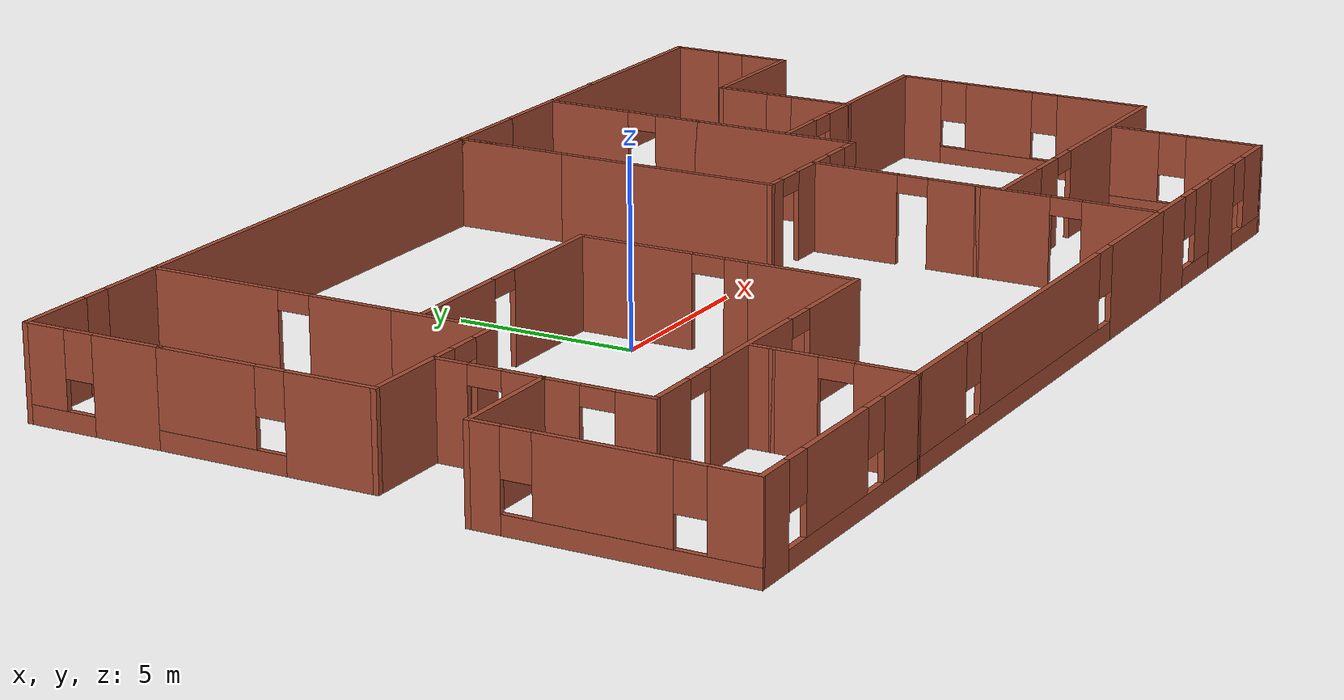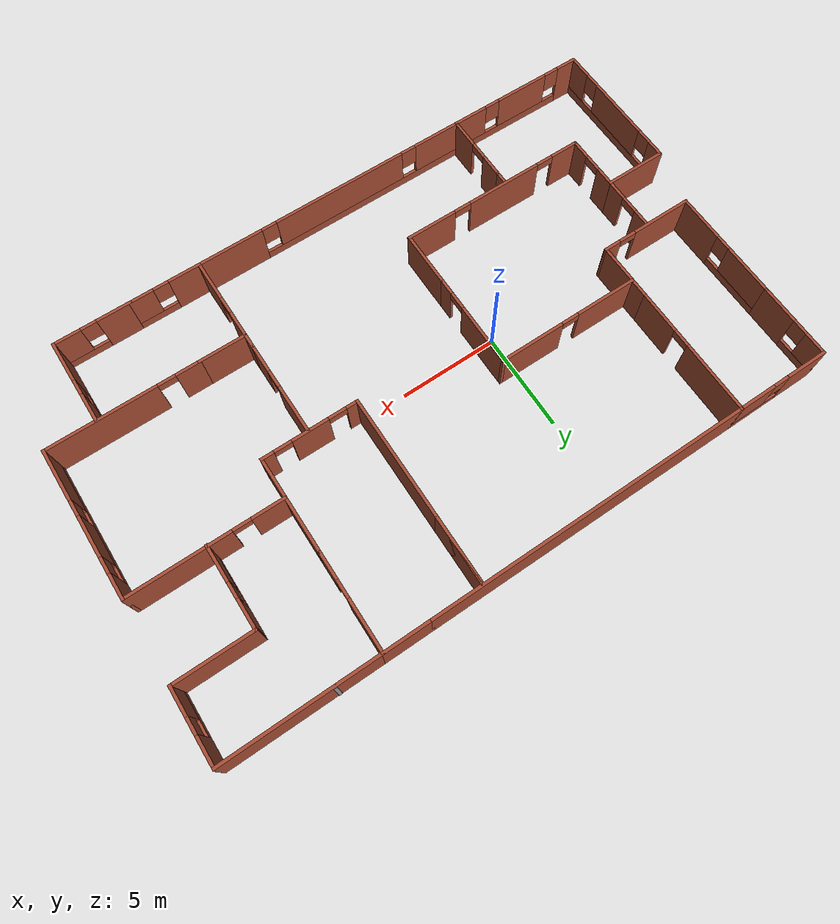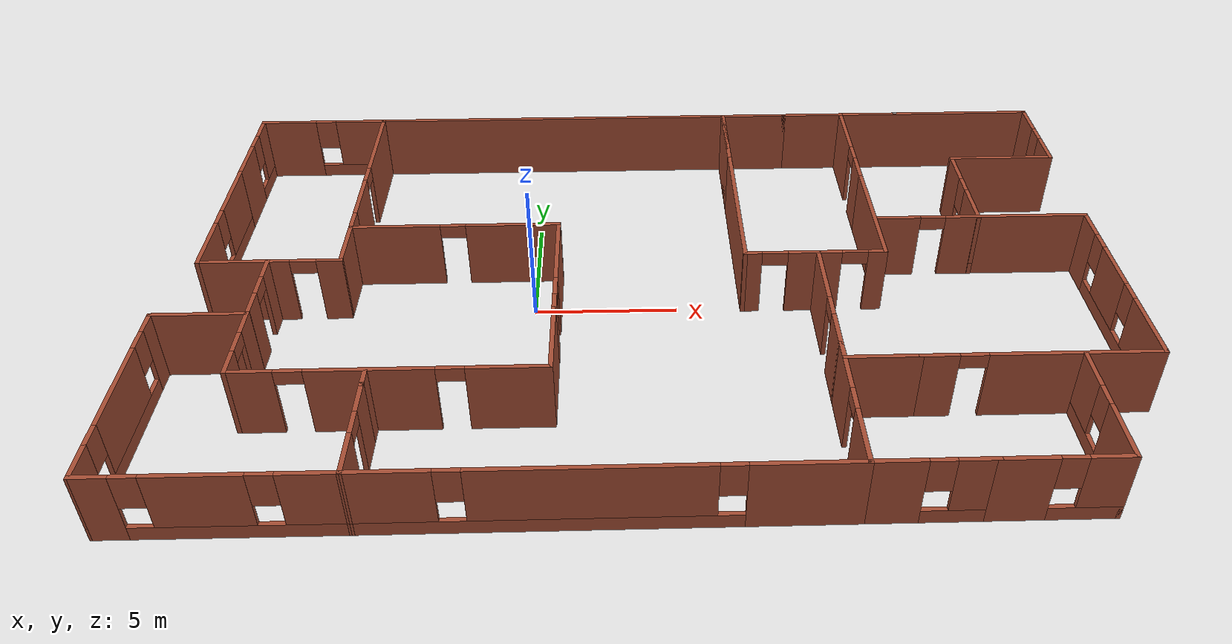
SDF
<?xml version='1.0'?>
<sdf version='1.6'>
  <model name='office'>
    <pose frame=''>3.86148 -0.195271 0 0 -0 0</pose>
    <link name='Wall_0'>
      <pose frame=''>-12.8016 9.8293 0 0 -0 1.2e-05</pose>
      <visual name='Wall_0_Visual_0'>
        <pose frame=''>-1.40419 0 1.25 0 -0 0</pose>
        <geometry>
          <box>
            <size>2.19162 0.15 2.5</size>
          </box>
        </geometry>
        <material>
          <script>
            <uri>file://media/materials/scripts/gazebo.material</uri>
            <name>Gazebo/Bricks</name>
          </script>
          <ambient>1 1 1 1</ambient>
        </material>
        <meta>
          <layer>0</layer>
        </meta>
      </visual>
      <collision name='Wall_0_Collision_0'>
        <geometry>
          <box>
            <size>2.19162 0.15 2.5</size>
          </box>
        </geometry>
        <pose frame=''>-1.40419 0 1.25 0 -0 0</pose>
      </collision>
      <visual name='Wall_0_Visual_1'>
        <pose frame=''>1.09581 0 0.25 0 -0 0</pose>
        <geometry>
          <box>
            <size>2.80838 0.15 0.5</size>
          </box>
        </geometry>
        <material>
          <script>
            <uri>file://media/materials/scripts/gazebo.material</uri>
            <name>Gazebo/Bricks</name>
          </script>
          <ambient>1 1 1 1</ambient>
        </material>
        <meta>
          <layer>0</layer>
        </meta>
      </visual>
      <collision name='Wall_0_Collision_1'>
        <geometry>
          <box>
            <size>2.80838 0.15 0.5</size>
          </box>
        </geometry>
        <pose frame=''>1.09581 0 0.25 0 -0 0</pose>
      </collision>
      <visual name='Wall_0_Visual_2'>
        <pose frame=''>1.49581 0 1.5 0 -0 0</pose>
        <geometry>
          <box>
            <size>2.00839 0.15 2</size>
          </box>
        </geometry>
        <material>
          <script>
            <uri>file://media/materials/scripts/gazebo.material</uri>
            <name>Gazebo/Bricks</name>
          </script>
          <ambient>1 1 1 1</ambient>
        </material>
        <meta>
          <layer>0</layer>
        </meta>
      </visual>
      <collision name='Wall_0_Collision_2'>
        <geometry>
          <box>
            <size>2.00839 0.15 2</size>
          </box>
        </geometry>
        <pose frame=''>1.49581 0 1.5 0 -0 0</pose>
      </collision>
      <visual name='Wall_0_Visual_3'>
        <pose frame=''>0.091615 0 1.9 0 -0 0</pose>
        <geometry>
          <box>
            <size>0.8 0.15 1.2</size>
          </box>
        </geometry>
        <material>
          <script>
            <uri>file://media/materials/scripts/gazebo.material</uri>
            <name>Gazebo/Bricks</name>
          </script>
          <ambient>1 1 1 1</ambient>
        </material>
        <meta>
          <layer>0</layer>
        </meta>
      </visual>
      <collision name='Wall_0_Collision_3'>
        <geometry>
          <box>
            <size>0.8 0.15 1.2</size>
          </box>
        </geometry>
        <pose frame=''>0.091615 0 1.9 0 -0 0</pose>
      </collision>
    </link>
    <link name='Wall_1'>
      <pose frame=''>-10.3767 6.40433 0 0 0 -1.5708</pose>
      <visual name='Wall_1_Visual_0'>
        <pose frame=''>-1.61827 0 1.25 0 -0 0</pose>
        <geometry>
          <box>
            <size>3.76346 0.15 2.5</size>
          </box>
        </geometry>
        <material>
          <script>
            <uri>file://media/materials/scripts/gazebo.material</uri>
            <name>Gazebo/Bricks</name>
          </script>
          <ambient>0 0 1 1</ambient>
        </material>
        <meta>
          <layer>0</layer>
        </meta>
      </visual>
      <collision name='Wall_1_Collision_0'>
        <geometry>
          <box>
            <size>3.76346 0.15 2.5</size>
          </box>
        </geometry>
        <pose frame=''>-1.61827 0 1.25 0 -0 0</pose>
      </collision>
      <visual name='Wall_1_Visual_1'>
        <pose frame=''>2.33173 0 1.25 0 -0 0</pose>
        <geometry>
          <box>
            <size>2.33654 0.15 2.5</size>
          </box>
        </geometry>
        <material>
          <script>
            <uri>file://media/materials/scripts/gazebo.material</uri>
            <name>Gazebo/Bricks</name>
          </script>
          <ambient>0 0 1 1</ambient>
        </material>
        <meta>
          <layer>0</layer>
        </meta>
      </visual>
      <collision name='Wall_1_Collision_1'>
        <geometry>
          <box>
            <size>2.33654 0.15 2.5</size>
          </box>
        </geometry>
        <pose frame=''>2.33173 0 1.25 0 -0 0</pose>
      </collision>
      <visual name='Wall_1_Visual_2'>
        <pose frame=''>0.713457 0 2.25 0 -0 0</pose>
        <geometry>
          <box>
            <size>0.9 0.15 0.5</size>
          </box>
        </geometry>
        <material>
          <script>
            <uri>file://media/materials/scripts/gazebo.material</uri>
            <name>Gazebo/Bricks</name>
          </script>
          <ambient>0 0 1 1</ambient>
        </material>
        <meta>
          <layer>0</layer>
        </meta>
      </visual>
      <collision name='Wall_1_Collision_2'>
        <geometry>
          <box>
            <size>0.9 0.15 0.5</size>
          </box>
        </geometry>
        <pose frame=''>0.713457 0 2.25 0 -0 0</pose>
      </collision>
    </link>
    <link name='Wall_10'>
      <collision name='Wall_10_Collision'>
        <geometry>
          <box>
            <size>3 0.15 2.5</size>
          </box>
        </geometry>
        <pose frame=''>0 0 1.25 0 -0 0</pose>
      </collision>
      <visual name='Wall_10_Visual'>
        <pose frame=''>0 0 1.25 0 -0 0</pose>
        <geometry>
          <box>
            <size>3 0.15 2.5</size>
          </box>
        </geometry>
        <material>
          <script>
            <uri>file://media/materials/scripts/gazebo.material</uri>
            <name>Gazebo/Bricks</name>
          </script>
          <ambient>0 0 1 1</ambient>
        </material>
        <meta>
          <layer>0</layer>
        </meta>
      </visual>
      <pose frame=''>-3.00328 -4.16052 0 0 -0 1.5708</pose>
    </link>
    <link name='Wall_11'>
      <pose frame=''>-3.00328 -0.310524 0 0 -0 1.5708</pose>
      <visual name='Wall_11_Visual_0'>
        <pose frame=''>-2.09105 0 1.25 0 -0 0</pose>
        <geometry>
          <box>
            <size>0.817909 0.15 2.5</size>
          </box>
        </geometry>
        <material>
          <script>
            <uri>file://media/materials/scripts/gazebo.material</uri>
            <name>Gazebo/Bricks</name>
          </script>
          <ambient>0 0 1 1</ambient>
        </material>
        <meta>
          <layer>0</layer>
        </meta>
      </visual>
      <collision name='Wall_11_Collision_0'>
        <geometry>
          <box>
            <size>0.817909 0.15 2.5</size>
          </box>
        </geometry>
        <pose frame=''>-2.09105 0 1.25 0 -0 0</pose>
      </collision>
      <visual name='Wall_11_Visual_1'>
        <pose frame=''>0.858954 0 1.25 0 -0 0</pose>
        <geometry>
          <box>
            <size>3.28209 0.15 2.5</size>
          </box>
        </geometry>
        <material>
          <script>
            <uri>file://media/materials/scripts/gazebo.material</uri>
            <name>Gazebo/Bricks</name>
          </script>
          <ambient>0 0 1 1</ambient>
        </material>
        <meta>
          <layer>0</layer>
        </meta>
      </visual>
      <collision name='Wall_11_Collision_1'>
        <geometry>
          <box>
            <size>3.28209 0.15 2.5</size>
          </box>
        </geometry>
        <pose frame=''>0.858954 0 1.25 0 -0 0</pose>
      </collision>
      <visual name='Wall_11_Visual_2'>
        <pose frame=''>-1.23209 0 2.25 0 -0 0</pose>
        <geometry>
          <box>
            <size>0.9 0.15 0.5</size>
          </box>
        </geometry>
        <material>
          <script>
            <uri>file://media/materials/scripts/gazebo.material</uri>
            <name>Gazebo/Bricks</name>
          </script>
          <ambient>0 0 1 1</ambient>
        </material>
        <meta>
          <layer>0</layer>
        </meta>
      </visual>
      <collision name='Wall_11_Collision_2'>
        <geometry>
          <box>
            <size>0.9 0.15 0.5</size>
          </box>
        </geometry>
        <pose frame=''>-1.23209 0 2.25 0 -0 0</pose>
      </collision>
    </link>
    <link name='Wall_12'>
      <pose frame=''>-6.67828 2.11448 0 0 -0 3.14159</pose>
      <visual name='Wall_12_Visual_0'>
        <pose frame=''>-2.05802 0 1.25 0 -0 0</pose>
        <geometry>
          <box>
            <size>3.38397 0.15 2.5</size>
          </box>
        </geometry>
        <material>
          <script>
            <uri>file://media/materials/scripts/gazebo.material</uri>
            <name>Gazebo/Bricks</name>
          </script>
          <ambient>0 0 1 1</ambient>
        </material>
        <meta>
          <layer>0</layer>
        </meta>
      </visual>
      <collision name='Wall_12_Collision_0'>
        <geometry>
          <box>
            <size>3.38397 0.15 2.5</size>
          </box>
        </geometry>
        <pose frame=''>-2.05802 0 1.25 0 -0 0</pose>
      </collision>
      <visual name='Wall_12_Visual_1'>
        <pose frame=''>2.14199 0 1.25 0 -0 0</pose>
        <geometry>
          <box>
            <size>3.21603 0.15 2.5</size>
          </box>
        </geometry>
        <material>
          <script>
            <uri>file://media/materials/scripts/gazebo.material</uri>
            <name>Gazebo/Bricks</name>
          </script>
          <ambient>0 0 1 1</ambient>
        </material>
        <meta>
          <layer>0</layer>
        </meta>
      </visual>
      <collision name='Wall_12_Collision_1'>
        <geometry>
          <box>
            <size>3.21603 0.15 2.5</size>
          </box>
        </geometry>
        <pose frame=''>2.14199 0 1.25 0 -0 0</pose>
      </collision>
      <visual name='Wall_12_Visual_2'>
        <pose frame=''>0.083969 0 2.25 0 -0 0</pose>
        <geometry>
          <box>
            <size>0.9 0.15 0.5</size>
          </box>
        </geometry>
        <material>
          <script>
            <uri>file://media/materials/scripts/gazebo.material</uri>
            <name>Gazebo/Bricks</name>
          </script>
          <ambient>0 0 1 1</ambient>
        </material>
        <meta>
          <layer>0</layer>
        </meta>
      </visual>
      <collision name='Wall_12_Collision_2'>
        <geometry>
          <box>
            <size>0.9 0.15 0.5</size>
          </box>
        </geometry>
        <pose frame=''>0.083969 0 2.25 0 -0 0</pose>
      </collision>
    </link>
    <link name='Wall_14'>
      <collision name='Wall_14_Collision'>
        <geometry>
          <box>
            <size>16.5 0.15 2.5</size>
          </box>
        </geometry>
        <pose frame=''>0 0 1.25 0 -0 0</pose>
      </collision>
      <visual name='Wall_14_Visual'>
        <pose frame=''>0 0 1.25 0 -0 0</pose>
        <geometry>
          <box>
            <size>16.5 0.15 2.5</size>
          </box>
        </geometry>
        <material>
          <script>
            <uri>file://media/materials/scripts/gazebo.material</uri>
            <name>Gazebo/Bricks</name>
          </script>
          <ambient>1 1 1 1</ambient>
        </material>
        <meta>
          <layer>0</layer>
        </meta>
      </visual>
      <pose frame=''>-2.20168 9.82933 0 0 -0 0</pose>
    </link>
    <link name='Wall_15'>
      <collision name='Wall_15_Collision'>
        <geometry>
          <box>
            <size>2.5 0.15 2.5</size>
          </box>
        </geometry>
        <pose frame=''>0 0 1.25 0 -0 0</pose>
      </collision>
      <visual name='Wall_15_Visual'>
        <pose frame=''>0 0 1.25 0 -0 0</pose>
        <geometry>
          <box>
            <size>2.5 0.15 2.5</size>
          </box>
        </geometry>
        <material>
          <script>
            <uri>file://media/materials/scripts/gazebo.material</uri>
            <name>Gazebo/Bricks</name>
          </script>
          <ambient>1 1 1 1</ambient>
        </material>
        <meta>
          <layer>0</layer>
        </meta>
      </visual>
      <pose frame=''>7.14832 9.82933 0 0 -0 0</pose>
    </link>
    <link name='Wall_150'>
      <collision name='Wall_150_Collision'>
        <geometry>
          <box>
            <size>7.75 0.15 2.5</size>
          </box>
        </geometry>
        <pose frame=''>0 0 1.25 0 -0 0</pose>
      </collision>
      <visual name='Wall_150_Visual'>
        <pose frame=''>0 0 1.25 0 -0 0</pose>
        <geometry>
          <box>
            <size>7.75 0.15 2.5</size>
          </box>
        </geometry>
        <material>
          <script>
            <uri>file://media/materials/scripts/gazebo.material</uri>
            <name>Gazebo/Bricks</name>
          </script>
          <ambient>1 1 1 1</ambient>
        </material>
        <meta>
          <layer>0</layer>
        </meta>
      </visual>
      <pose frame=''>12.1233 9.82933 0 0 -0 0</pose>
    </link>
    <link name='Wall_151'>
      <pose frame=''>15.9233 8.02933 0 0 0 -1.5708</pose>
      <visual name='Wall_151_Visual_0'>
        <pose frame=''>-1.12763 0 1.25 0 -0 0</pose>
        <geometry>
          <box>
            <size>1.49474 0.15 2.5</size>
          </box>
        </geometry>
        <material>
          <script>
            <uri>file://media/materials/scripts/gazebo.material</uri>
            <name>Gazebo/Bricks</name>
          </script>
          <ambient>1 1 1 1</ambient>
        </material>
        <meta>
          <layer>0</layer>
        </meta>
      </visual>
      <collision name='Wall_151_Collision_0'>
        <geometry>
          <box>
            <size>1.49474 0.15 2.5</size>
          </box>
        </geometry>
        <pose frame=''>-1.12763 0 1.25 0 -0 0</pose>
      </collision>
      <visual name='Wall_151_Visual_1'>
        <pose frame=''>0.747372 0 0.25 0 -0 0</pose>
        <geometry>
          <box>
            <size>2.25526 0.15 0.5</size>
          </box>
        </geometry>
        <material>
          <script>
            <uri>file://media/materials/scripts/gazebo.material</uri>
            <name>Gazebo/Bricks</name>
          </script>
          <ambient>1 1 1 1</ambient>
        </material>
        <meta>
          <layer>0</layer>
        </meta>
      </visual>
      <collision name='Wall_151_Collision_1'>
        <geometry>
          <box>
            <size>2.25526 0.15 0.5</size>
          </box>
        </geometry>
        <pose frame=''>0.747372 0 0.25 0 -0 0</pose>
      </collision>
      <visual name='Wall_151_Visual_2'>
        <pose frame=''>1.14737 0 1.5 0 -0 0</pose>
        <geometry>
          <box>
            <size>1.45526 0.15 2</size>
          </box>
        </geometry>
        <material>
          <script>
            <uri>file://media/materials/scripts/gazebo.material</uri>
            <name>Gazebo/Bricks</name>
          </script>
          <ambient>1 1 1 1</ambient>
        </material>
        <meta>
          <layer>0</layer>
        </meta>
      </visual>
      <collision name='Wall_151_Collision_2'>
        <geometry>
          <box>
            <size>1.45526 0.15 2</size>
          </box>
        </geometry>
        <pose frame=''>1.14737 0 1.5 0 -0 0</pose>
      </collision>
      <visual name='Wall_151_Visual_3'>
        <pose frame=''>0.019743 0 1.9 0 -0 0</pose>
        <geometry>
          <box>
            <size>0.8 0.15 1.2</size>
          </box>
        </geometry>
        <material>
          <script>
            <uri>file://media/materials/scripts/gazebo.material</uri>
            <name>Gazebo/Bricks</name>
          </script>
          <ambient>1 1 1 1</ambient>
        </material>
        <meta>
          <layer>0</layer>
        </meta>
      </visual>
      <collision name='Wall_151_Collision_3'>
        <geometry>
          <box>
            <size>0.8 0.15 1.2</size>
          </box>
        </geometry>
        <pose frame=''>0.019743 0 1.9 0 -0 0</pose>
      </collision>
    </link>
    <link name='Wall_152'>
      <collision name='Wall_152_Collision'>
        <geometry>
          <box>
            <size>4 0.15 2.5</size>
          </box>
        </geometry>
        <pose frame=''>0 0 1.25 0 -0 0</pose>
      </collision>
      <visual name='Wall_152_Visual'>
        <pose frame=''>0 0 1.25 0 -0 0</pose>
        <geometry>
          <box>
            <size>4 0.15 2.5</size>
          </box>
        </geometry>
        <material>
          <script>
            <uri>file://media/materials/scripts/gazebo.material</uri>
            <name>Gazebo/Bricks</name>
          </script>
          <ambient>1 1 1 1</ambient>
        </material>
        <meta>
          <layer>0</layer>
        </meta>
      </visual>
      <pose frame=''>13.9983 6.22933 0 0 -0 3.14159</pose>
    </link>
    <link name='Wall_156'>
      <pose frame=''>12.0733 4.17933 0 0 0 -1.5708</pose>
      <visual name='Wall_156_Visual_0'>
        <pose frame=''>-1.33794 0 1.25 0 -0 0</pose>
        <geometry>
          <box>
            <size>1.57411 0.15 2.5</size>
          </box>
        </geometry>
        <material>
          <script>
            <uri>file://media/materials/scripts/gazebo.material</uri>
            <name>Gazebo/Bricks</name>
          </script>
          <ambient>1 1 1 1</ambient>
        </material>
        <meta>
          <layer>0</layer>
        </meta>
      </visual>
      <collision name='Wall_156_Collision_0'>
        <geometry>
          <box>
            <size>1.57411 0.15 2.5</size>
          </box>
        </geometry>
        <pose frame=''>-1.33794 0 1.25 0 -0 0</pose>
      </collision>
      <visual name='Wall_156_Visual_1'>
        <pose frame=''>0.787055 0 0.25 0 -0 0</pose>
        <geometry>
          <box>
            <size>2.67589 0.15 0.5</size>
          </box>
        </geometry>
        <material>
          <script>
            <uri>file://media/materials/scripts/gazebo.material</uri>
            <name>Gazebo/Bricks</name>
          </script>
          <ambient>1 1 1 1</ambient>
        </material>
        <meta>
          <layer>0</layer>
        </meta>
      </visual>
      <collision name='Wall_156_Collision_1'>
        <geometry>
          <box>
            <size>2.67589 0.15 0.5</size>
          </box>
        </geometry>
        <pose frame=''>0.787055 0 0.25 0 -0 0</pose>
      </collision>
      <visual name='Wall_156_Visual_2'>
        <pose frame=''>1.18705 0 1.5 0 -0 0</pose>
        <geometry>
          <box>
            <size>1.87589 0.15 2</size>
          </box>
        </geometry>
        <material>
          <script>
            <uri>file://media/materials/scripts/gazebo.material</uri>
            <name>Gazebo/Bricks</name>
          </script>
          <ambient>1 1 1 1</ambient>
        </material>
        <meta>
          <layer>0</layer>
        </meta>
      </visual>
      <collision name='Wall_156_Collision_2'>
        <geometry>
          <box>
            <size>1.87589 0.15 2</size>
          </box>
        </geometry>
        <pose frame=''>1.18705 0 1.5 0 -0 0</pose>
      </collision>
      <visual name='Wall_156_Visual_3'>
        <pose frame=''>-0.150889 0 1.9 0 -0 0</pose>
        <geometry>
          <box>
            <size>0.8 0.15 1.2</size>
          </box>
        </geometry>
        <material>
          <script>
            <uri>file://media/materials/scripts/gazebo.material</uri>
            <name>Gazebo/Bricks</name>
          </script>
          <ambient>1 1 1 1</ambient>
        </material>
        <meta>
          <layer>0</layer>
        </meta>
      </visual>
      <collision name='Wall_156_Collision_3'>
        <geometry>
          <box>
            <size>0.8 0.15 1.2</size>
          </box>
        </geometry>
        <pose frame=''>-0.150889 0 1.9 0 -0 0</pose>
      </collision>
    </link>
    <link name='Wall_16'>
      <pose frame=''>8.32342 7.4043 0 0 0 -1.57075</pose>
      <visual name='Wall_16_Visual_0'>
        <pose frame=''>-1.16357 0 1.25 0 -0 0</pose>
        <geometry>
          <box>
            <size>2.67286 0.15 2.5</size>
          </box>
        </geometry>
        <material>
          <script>
            <uri>file://media/materials/scripts/gazebo.material</uri>
            <name>Gazebo/Bricks</name>
          </script>
          <ambient>0 0 1 1</ambient>
        </material>
        <meta>
          <layer>0</layer>
        </meta>
      </visual>
      <collision name='Wall_16_Collision_0'>
        <geometry>
          <box>
            <size>2.67286 0.15 2.5</size>
          </box>
        </geometry>
        <pose frame=''>-1.16357 0 1.25 0 -0 0</pose>
      </collision>
      <visual name='Wall_16_Visual_1'>
        <pose frame=''>1.78643 0 1.25 0 -0 0</pose>
        <geometry>
          <box>
            <size>1.42714 0.15 2.5</size>
          </box>
        </geometry>
        <material>
          <script>
            <uri>file://media/materials/scripts/gazebo.material</uri>
            <name>Gazebo/Bricks</name>
          </script>
          <ambient>0 0 1 1</ambient>
        </material>
        <meta>
          <layer>0</layer>
        </meta>
      </visual>
      <collision name='Wall_16_Collision_1'>
        <geometry>
          <box>
            <size>1.42714 0.15 2.5</size>
          </box>
        </geometry>
        <pose frame=''>1.78643 0 1.25 0 -0 0</pose>
      </collision>
      <visual name='Wall_16_Visual_2'>
        <pose frame=''>0.622857 0 2.25 0 -0 0</pose>
        <geometry>
          <box>
            <size>0.9 0.15 0.5</size>
          </box>
        </geometry>
        <material>
          <script>
            <uri>file://media/materials/scripts/gazebo.material</uri>
            <name>Gazebo/Bricks</name>
          </script>
          <ambient>0 0 1 1</ambient>
        </material>
        <meta>
          <layer>0</layer>
        </meta>
      </visual>
      <collision name='Wall_16_Collision_2'>
        <geometry>
          <box>
            <size>0.9 0.15 0.5</size>
          </box>
        </geometry>
        <pose frame=''>0.622857 0 2.25 0 -0 0</pose>
      </collision>
    </link>
    <link name='Wall_17'>
      <collision name='Wall_17_Collision'>
        <geometry>
          <box>
            <size>5 0.15 2.5</size>
          </box>
        </geometry>
        <pose frame=''>0 0 1.25 0 -0 0</pose>
      </collision>
      <visual name='Wall_17_Visual'>
        <pose frame=''>0 0 1.25 0 -0 0</pose>
        <geometry>
          <box>
            <size>5 0.15 2.5</size>
          </box>
        </geometry>
        <material>
          <script>
            <uri>file://media/materials/scripts/gazebo.material</uri>
            <name>Gazebo/Bricks</name>
          </script>
          <ambient>0 0 1 1</ambient>
        </material>
        <meta>
          <layer>0</layer>
        </meta>
      </visual>
      <pose frame=''>8.32352 2.55427 0 0 0 -1.5708</pose>
    </link>
    <link name='Wall_18'>
      <pose frame=''>5.89852 0.129271 0 0 -0 3.14159</pose>
      <visual name='Wall_18_Visual_0'>
        <pose frame=''>-2.16272 0 1.25 0 -0 0</pose>
        <geometry>
          <box>
            <size>0.674563 0.15 2.5</size>
          </box>
        </geometry>
        <material>
          <script>
            <uri>file://media/materials/scripts/gazebo.material</uri>
            <name>Gazebo/Bricks</name>
          </script>
          <ambient>0 0 1 1</ambient>
        </material>
        <meta>
          <layer>0</layer>
        </meta>
      </visual>
      <collision name='Wall_18_Collision_0'>
        <geometry>
          <box>
            <size>0.674563 0.15 2.5</size>
          </box>
        </geometry>
        <pose frame=''>-2.16272 0 1.25 0 -0 0</pose>
      </collision>
      <visual name='Wall_18_Visual_1'>
        <pose frame=''>0.007773 0 1.25 0 -0 0</pose>
        <geometry>
          <box>
            <size>1.86642 0.15 2.5</size>
          </box>
        </geometry>
        <material>
          <script>
            <uri>file://media/materials/scripts/gazebo.material</uri>
            <name>Gazebo/Bricks</name>
          </script>
          <ambient>0 0 1 1</ambient>
        </material>
        <meta>
          <layer>0</layer>
        </meta>
      </visual>
      <collision name='Wall_18_Collision_1'>
        <geometry>
          <box>
            <size>1.86642 0.15 2.5</size>
          </box>
        </geometry>
        <pose frame=''>0.007773 0 1.25 0 -0 0</pose>
      </collision>
      <visual name='Wall_18_Visual_2'>
        <pose frame=''>2.17049 0 1.25 0 -0 0</pose>
        <geometry>
          <box>
            <size>0.659016 0.15 2.5</size>
          </box>
        </geometry>
        <material>
          <script>
            <uri>file://media/materials/scripts/gazebo.material</uri>
            <name>Gazebo/Bricks</name>
          </script>
          <ambient>0 0 1 1</ambient>
        </material>
        <meta>
          <layer>0</layer>
        </meta>
      </visual>
      <collision name='Wall_18_Collision_2'>
        <geometry>
          <box>
            <size>0.659016 0.15 2.5</size>
          </box>
        </geometry>
        <pose frame=''>2.17049 0 1.25 0 -0 0</pose>
      </collision>
      <visual name='Wall_18_Visual_3'>
        <pose frame=''>-1.37544 0 2.25 0 -0 0</pose>
        <geometry>
          <box>
            <size>0.9 0.15 0.5</size>
          </box>
        </geometry>
        <material>
          <script>
            <uri>file://media/materials/scripts/gazebo.material</uri>
            <name>Gazebo/Bricks</name>
          </script>
          <ambient>0 0 1 1</ambient>
        </material>
        <meta>
          <layer>0</layer>
        </meta>
      </visual>
      <collision name='Wall_18_Collision_3'>
        <geometry>
          <box>
            <size>0.9 0.15 0.5</size>
          </box>
        </geometry>
        <pose frame=''>-1.37544 0 2.25 0 -0 0</pose>
      </collision>
      <visual name='Wall_18_Visual_4'>
        <pose frame=''>1.39098 0 2.25 0 -0 0</pose>
        <geometry>
          <box>
            <size>0.9 0.15 0.5</size>
          </box>
        </geometry>
        <material>
          <script>
            <uri>file://media/materials/scripts/gazebo.material</uri>
            <name>Gazebo/Bricks</name>
          </script>
          <ambient>0 0 1 1</ambient>
        </material>
        <meta>
          <layer>0</layer>
        </meta>
      </visual>
      <collision name='Wall_18_Collision_4'>
        <geometry>
          <box>
            <size>0.9 0.15 0.5</size>
          </box>
        </geometry>
        <pose frame=''>1.39098 0 2.25 0 -0 0</pose>
      </collision>
    </link>
    <link name='Wall_19'>
      <collision name='Wall_19_Collision'>
        <geometry>
          <box>
            <size>6.5 0.15 2.5</size>
          </box>
        </geometry>
        <pose frame=''>0 0 1.25 0 -0 0</pose>
      </collision>
      <visual name='Wall_19_Visual'>
        <pose frame=''>0 0 1.25 0 -0 0</pose>
        <geometry>
          <box>
            <size>6.5 0.15 2.5</size>
          </box>
        </geometry>
        <material>
          <script>
            <uri>file://media/materials/scripts/gazebo.material</uri>
            <name>Gazebo/Bricks</name>
          </script>
          <ambient>0 0 1 1</ambient>
        </material>
        <meta>
          <layer>0</layer>
        </meta>
      </visual>
      <pose frame=''>3.47352 3.30427 0 0 -0 1.5708</pose>
    </link>
    <link name='Wall_2'>
      <collision name='Wall_2_Collision'>
        <geometry>
          <box>
            <size>3 0.15 2.5</size>
          </box>
        </geometry>
        <pose frame=''>0 0 1.25 0 -0 0</pose>
      </collision>
      <visual name='Wall_2_Visual'>
        <pose frame=''>0 0 1.25 0 -0 0</pose>
        <geometry>
          <box>
            <size>3 0.15 2.5</size>
          </box>
        </geometry>
        <material>
          <script>
            <uri>file://media/materials/scripts/gazebo.material</uri>
            <name>Gazebo/Bricks</name>
          </script>
          <ambient>0 0 1 1</ambient>
        </material>
        <meta>
          <layer>0</layer>
        </meta>
      </visual>
      <pose frame=''>-10.3766 1.5543 0 0 0 -1.57073</pose>
    </link>
    <link name='Wall_20'>
      <pose frame=''>3.47342 8.1543 0 0 -0 1.57086</pose>
      <visual name='Wall_20_Visual_0'>
        <pose frame=''>0 0 1.25 0 -0 0</pose>
        <geometry>
          <box>
            <size>3.5 0.15 2.5</size>
          </box>
        </geometry>
        <material>
          <script>
            <uri>file://media/materials/scripts/gazebo.material</uri>
            <name>Gazebo/Bricks</name>
          </script>
          <ambient>0 0 1 1</ambient>
        </material>
        <meta>
          <layer>0</layer>
        </meta>
      </visual>
      <collision name='Wall_20_Collision_0'>
        <geometry>
          <box>
            <size>3.5 0.15 2.5</size>
          </box>
        </geometry>
        <pose frame=''>0 0 1.25 0 -0 0</pose>
      </collision>
      <visual name='Wall_20_Visual_1'>
        <pose frame=''>0.400263 0 1.25 0 -0 0</pose>
        <geometry>
          <box>
            <size>2.69948 0.15 2.5</size>
          </box>
        </geometry>
        <material>
          <script>
            <uri>file://media/materials/scripts/gazebo.material</uri>
            <name>Gazebo/Bricks</name>
          </script>
          <ambient>0 0 1 1</ambient>
        </material>
        <meta>
          <layer>0</layer>
        </meta>
      </visual>
      <collision name='Wall_20_Collision_1'>
        <geometry>
          <box>
            <size>2.69948 0.15 2.5</size>
          </box>
        </geometry>
        <pose frame=''>0.400263 0 1.25 0 -0 0</pose>
      </collision>
    </link>
    <link name='Wall_22'>
      <pose frame=''>5.99314 -2.33064 0 0 0 -1.5708</pose>
      <visual name='Wall_22_Visual_0'>
        <pose frame=''>-1.21642 0 1.25 0 -0 0</pose>
        <geometry>
          <box>
            <size>2.56715 0.15 2.5</size>
          </box>
        </geometry>
        <material>
          <script>
            <uri>file://media/materials/scripts/gazebo.material</uri>
            <name>Gazebo/Bricks</name>
          </script>
          <ambient>1 1 1 1</ambient>
        </material>
        <meta>
          <layer>0</layer>
        </meta>
      </visual>
      <collision name='Wall_22_Collision_0'>
        <geometry>
          <box>
            <size>2.56715 0.15 2.5</size>
          </box>
        </geometry>
        <pose frame=''>-1.21642 0 1.25 0 -0 0</pose>
      </collision>
      <visual name='Wall_22_Visual_1'>
        <pose frame=''>1.73358 0 1.25 0 -0 0</pose>
        <geometry>
          <box>
            <size>1.53285 0.15 2.5</size>
          </box>
        </geometry>
        <material>
          <script>
            <uri>file://media/materials/scripts/gazebo.material</uri>
            <name>Gazebo/Bricks</name>
          </script>
          <ambient>1 1 1 1</ambient>
        </material>
        <meta>
          <layer>0</layer>
        </meta>
      </visual>
      <collision name='Wall_22_Collision_1'>
        <geometry>
          <box>
            <size>1.53285 0.15 2.5</size>
          </box>
        </geometry>
        <pose frame=''>1.73358 0 1.25 0 -0 0</pose>
      </collision>
      <visual name='Wall_22_Visual_2'>
        <pose frame=''>0.517152 0 2.25 0 -0 0</pose>
        <geometry>
          <box>
            <size>0.9 0.15 0.5</size>
          </box>
        </geometry>
        <material>
          <script>
            <uri>file://media/materials/scripts/gazebo.material</uri>
            <name>Gazebo/Bricks</name>
          </script>
          <ambient>1 1 1 1</ambient>
        </material>
        <meta>
          <layer>0</layer>
        </meta>
      </visual>
      <collision name='Wall_22_Collision_2'>
        <geometry>
          <box>
            <size>0.9 0.15 0.5</size>
          </box>
        </geometry>
        <pose frame=''>0.517152 0 2.25 0 -0 0</pose>
      </collision>
    </link>
    <link name='Wall_23'>
      <pose frame=''>5.99333 -7.30568 0 0 0 -1.57072</pose>
      <visual name='Wall_23_Visual_0'>
        <pose frame=''>-1.55338 0 1.25 0 -0 0</pose>
        <geometry>
          <box>
            <size>2.14324 0.15 2.5</size>
          </box>
        </geometry>
        <material>
          <script>
            <uri>file://media/materials/scripts/gazebo.material</uri>
            <name>Gazebo/Bricks</name>
          </script>
          <ambient>1 1 1 1</ambient>
        </material>
        <meta>
          <layer>0</layer>
        </meta>
      </visual>
      <collision name='Wall_23_Collision_0'>
        <geometry>
          <box>
            <size>2.14324 0.15 2.5</size>
          </box>
        </geometry>
        <pose frame=''>-1.55338 0 1.25 0 -0 0</pose>
      </collision>
      <visual name='Wall_23_Visual_1'>
        <pose frame=''>1.52162 0 1.25 0 -0 0</pose>
        <geometry>
          <box>
            <size>2.20676 0.15 2.5</size>
          </box>
        </geometry>
        <material>
          <script>
            <uri>file://media/materials/scripts/gazebo.material</uri>
            <name>Gazebo/Bricks</name>
          </script>
          <ambient>1 1 1 1</ambient>
        </material>
        <meta>
          <layer>0</layer>
        </meta>
      </visual>
      <collision name='Wall_23_Collision_1'>
        <geometry>
          <box>
            <size>2.20676 0.15 2.5</size>
          </box>
        </geometry>
        <pose frame=''>1.52162 0 1.25 0 -0 0</pose>
      </collision>
      <visual name='Wall_23_Visual_2'>
        <pose frame=''>-0.031758 0 2.25 0 -0 0</pose>
        <geometry>
          <box>
            <size>0.9 0.15 0.5</size>
          </box>
        </geometry>
        <material>
          <script>
            <uri>file://media/materials/scripts/gazebo.material</uri>
            <name>Gazebo/Bricks</name>
          </script>
          <ambient>1 1 1 1</ambient>
        </material>
        <meta>
          <layer>0</layer>
        </meta>
      </visual>
      <collision name='Wall_23_Collision_2'>
        <geometry>
          <box>
            <size>0.9 0.15 0.5</size>
          </box>
        </geometry>
        <pose frame=''>-0.031758 0 2.25 0 -0 0</pose>
      </collision>
    </link>
    <link name='Wall_24'>
      <pose frame=''>-1.30648 -9.85573 0 0 -0 3.14159</pose>
      <visual name='Wall_24_Visual_0'>
        <pose frame=''>-5.65269 0 1.25 0 -0 0</pose>
        <geometry>
          <box>
            <size>3.44462 0.15 2.5</size>
          </box>
        </geometry>
        <material>
          <script>
            <uri>file://media/materials/scripts/gazebo.material</uri>
            <name>Gazebo/Bricks</name>
          </script>
          <ambient>1 1 1 1</ambient>
        </material>
        <meta>
          <layer>0</layer>
        </meta>
      </visual>
      <collision name='Wall_24_Collision_0'>
        <geometry>
          <box>
            <size>3.44462 0.15 2.5</size>
          </box>
        </geometry>
        <pose frame=''>-5.65269 0 1.25 0 -0 0</pose>
      </collision>
      <visual name='Wall_24_Visual_1'>
        <pose frame=''>1.72231 0 0.25 0 -0 0</pose>
        <geometry>
          <box>
            <size>11.3054 0.15 0.5</size>
          </box>
        </geometry>
        <material>
          <script>
            <uri>file://media/materials/scripts/gazebo.material</uri>
            <name>Gazebo/Bricks</name>
          </script>
          <ambient>1 1 1 1</ambient>
        </material>
        <meta>
          <layer>0</layer>
        </meta>
      </visual>
      <collision name='Wall_24_Collision_1'>
        <geometry>
          <box>
            <size>11.3054 0.15 0.5</size>
          </box>
        </geometry>
        <pose frame=''>1.72231 0 0.25 0 -0 0</pose>
      </collision>
      <visual name='Wall_24_Visual_2'>
        <pose frame=''>0.432018 0 1.5 0 -0 0</pose>
        <geometry>
          <box>
            <size>7.12479 0.15 2</size>
          </box>
        </geometry>
        <material>
          <script>
            <uri>file://media/materials/scripts/gazebo.material</uri>
            <name>Gazebo/Bricks</name>
          </script>
          <ambient>1 1 1 1</ambient>
        </material>
        <meta>
          <layer>0</layer>
        </meta>
      </visual>
      <collision name='Wall_24_Collision_2'>
        <geometry>
          <box>
            <size>7.12479 0.15 2</size>
          </box>
        </geometry>
        <pose frame=''>0.432018 0 1.5 0 -0 0</pose>
      </collision>
      <visual name='Wall_24_Visual_3'>
        <pose frame=''>6.08471 0 1.5 0 -0 0</pose>
        <geometry>
          <box>
            <size>2.58059 0.15 2</size>
          </box>
        </geometry>
        <material>
          <script>
            <uri>file://media/materials/scripts/gazebo.material</uri>
            <name>Gazebo/Bricks</name>
          </script>
          <ambient>1 1 1 1</ambient>
        </material>
        <meta>
          <layer>0</layer>
        </meta>
      </visual>
      <collision name='Wall_24_Collision_3'>
        <geometry>
          <box>
            <size>2.58059 0.15 2</size>
          </box>
        </geometry>
        <pose frame=''>6.08471 0 1.5 0 -0 0</pose>
      </collision>
      <visual name='Wall_24_Visual_4'>
        <pose frame=''>-3.53038 0 1.9 0 -0 0</pose>
        <geometry>
          <box>
            <size>0.8 0.15 1.2</size>
          </box>
        </geometry>
        <material>
          <script>
            <uri>file://media/materials/scripts/gazebo.material</uri>
            <name>Gazebo/Bricks</name>
          </script>
          <ambient>1 1 1 1</ambient>
        </material>
        <meta>
          <layer>0</layer>
        </meta>
      </visual>
      <collision name='Wall_24_Collision_4'>
        <geometry>
          <box>
            <size>0.8 0.15 1.2</size>
          </box>
        </geometry>
        <pose frame=''>-3.53038 0 1.9 0 -0 0</pose>
      </collision>
      <visual name='Wall_24_Visual_5'>
        <pose frame=''>4.39441 0 1.9 0 -0 0</pose>
        <geometry>
          <box>
            <size>0.8 0.15 1.2</size>
          </box>
        </geometry>
        <material>
          <script>
            <uri>file://media/materials/scripts/gazebo.material</uri>
            <name>Gazebo/Bricks</name>
          </script>
          <ambient>1 1 1 1</ambient>
        </material>
        <meta>
          <layer>0</layer>
        </meta>
      </visual>
      <collision name='Wall_24_Collision_5'>
        <geometry>
          <box>
            <size>0.8 0.15 1.2</size>
          </box>
        </geometry>
        <pose frame=''>4.39441 0 1.9 0 -0 0</pose>
      </collision>
    </link>
    <link name='Wall_25'>
      <pose frame=''>-8.60667 -8.05568 0 0 -0 1.5709</pose>
      <visual name='Wall_25_Visual_0'>
        <pose frame=''>-1.07228 0 1.25 0 -0 0</pose>
        <geometry>
          <box>
            <size>1.60545 0.15 2.5</size>
          </box>
        </geometry>
        <material>
          <script>
            <uri>file://media/materials/scripts/gazebo.material</uri>
            <name>Gazebo/Bricks</name>
          </script>
          <ambient>1 1 1 1</ambient>
        </material>
        <meta>
          <layer>0</layer>
        </meta>
      </visual>
      <collision name='Wall_25_Collision_0'>
        <geometry>
          <box>
            <size>1.60545 0.15 2.5</size>
          </box>
        </geometry>
        <pose frame=''>-1.07228 0 1.25 0 -0 0</pose>
      </collision>
      <visual name='Wall_25_Visual_1'>
        <pose frame=''>1.25273 0 1.25 0 -0 0</pose>
        <geometry>
          <box>
            <size>1.24455 0.15 2.5</size>
          </box>
        </geometry>
        <material>
          <script>
            <uri>file://media/materials/scripts/gazebo.material</uri>
            <name>Gazebo/Bricks</name>
          </script>
          <ambient>1 1 1 1</ambient>
        </material>
        <meta>
          <layer>0</layer>
        </meta>
      </visual>
      <collision name='Wall_25_Collision_1'>
        <geometry>
          <box>
            <size>1.24455 0.15 2.5</size>
          </box>
        </geometry>
        <pose frame=''>1.25273 0 1.25 0 -0 0</pose>
      </collision>
      <visual name='Wall_25_Visual_2'>
        <pose frame=''>0.18045 0 2.25 0 -0 0</pose>
        <geometry>
          <box>
            <size>0.9 0.15 0.5</size>
          </box>
        </geometry>
        <material>
          <script>
            <uri>file://media/materials/scripts/gazebo.material</uri>
            <name>Gazebo/Bricks</name>
          </script>
          <ambient>1 1 1 1</ambient>
        </material>
        <meta>
          <layer>0</layer>
        </meta>
      </visual>
      <collision name='Wall_25_Collision_2'>
        <geometry>
          <box>
            <size>0.9 0.15 0.5</size>
          </box>
        </geometry>
        <pose frame=''>0.18045 0 2.25 0 -0 0</pose>
      </collision>
    </link>
    <link name='Wall_26'>
      <collision name='Wall_26_Collision'>
        <geometry>
          <box>
            <size>0.75 0.15 2.5</size>
          </box>
        </geometry>
        <pose frame=''>0 0 1.25 0 -0 0</pose>
      </collision>
      <visual name='Wall_26_Visual'>
        <pose frame=''>0 0 1.25 0 -0 0</pose>
        <geometry>
          <box>
            <size>0.75 0.15 2.5</size>
          </box>
        </geometry>
        <material>
          <script>
            <uri>file://media/materials/scripts/gazebo.material</uri>
            <name>Gazebo/Bricks</name>
          </script>
          <ambient>1 1 1 1</ambient>
        </material>
        <meta>
          <layer>0</layer>
        </meta>
      </visual>
      <pose frame=''>-8.60686 -5.95564 0 0 -0 1.5708</pose>
    </link>
    <link name='Wall_28'>
      <collision name='Wall_28_Collision'>
        <geometry>
          <box>
            <size>3.25 0.15 2.5</size>
          </box>
        </geometry>
        <pose frame=''>0 0 1.25 0 -0 0</pose>
      </collision>
      <visual name='Wall_28_Visual'>
        <pose frame=''>0 0 1.25 0 -0 0</pose>
        <geometry>
          <box>
            <size>3.25 0.15 2.5</size>
          </box>
        </geometry>
        <material>
          <script>
            <uri>file://media/materials/scripts/gazebo.material</uri>
            <name>Gazebo/Bricks</name>
          </script>
          <ambient>1 1 1 1</ambient>
        </material>
        <meta>
          <layer>0</layer>
        </meta>
      </visual>
      <pose frame=''>-14.4035 -2.73573 0 0 -0 3.14159</pose>
    </link>
    <link name='Wall_29'>
      <pose frame=''>-15.9535 -6.28573 0 0 0 -1.5708</pose>
      <visual name='Wall_29_Visual_0'>
        <pose frame=''>-3.17286 0 1.25 0 -0 0</pose>
        <geometry>
          <box>
            <size>0.904269 0.15 2.5</size>
          </box>
        </geometry>
        <material>
          <script>
            <uri>file://media/materials/scripts/gazebo.material</uri>
            <name>Gazebo/Bricks</name>
          </script>
          <ambient>1 1 1 1</ambient>
        </material>
        <meta>
          <layer>0</layer>
        </meta>
      </visual>
      <collision name='Wall_29_Collision_0'>
        <geometry>
          <box>
            <size>0.904269 0.15 2.5</size>
          </box>
        </geometry>
        <pose frame=''>-3.17286 0 1.25 0 -0 0</pose>
      </collision>
      <visual name='Wall_29_Visual_1'>
        <pose frame=''>0.452135 0 0.25 0 -0 0</pose>
        <geometry>
          <box>
            <size>6.34573 0.15 0.5</size>
          </box>
        </geometry>
        <material>
          <script>
            <uri>file://media/materials/scripts/gazebo.material</uri>
            <name>Gazebo/Bricks</name>
          </script>
          <ambient>1 1 1 1</ambient>
        </material>
        <meta>
          <layer>0</layer>
        </meta>
      </visual>
      <collision name='Wall_29_Collision_1'>
        <geometry>
          <box>
            <size>6.34573 0.15 0.5</size>
          </box>
        </geometry>
        <pose frame=''>0.452135 0 0.25 0 -0 0</pose>
      </collision>
      <visual name='Wall_29_Visual_2'>
        <pose frame=''>-0.206015 0 1.5 0 -0 0</pose>
        <geometry>
          <box>
            <size>3.42943 0.15 2</size>
          </box>
        </geometry>
        <material>
          <script>
            <uri>file://media/materials/scripts/gazebo.material</uri>
            <name>Gazebo/Bricks</name>
          </script>
          <ambient>1 1 1 1</ambient>
        </material>
        <meta>
          <layer>0</layer>
        </meta>
      </visual>
      <collision name='Wall_29_Collision_2'>
        <geometry>
          <box>
            <size>3.42943 0.15 2</size>
          </box>
        </geometry>
        <pose frame=''>-0.206015 0 1.5 0 -0 0</pose>
      </collision>
      <visual name='Wall_29_Visual_3'>
        <pose frame=''>2.96685 0 1.5 0 -0 0</pose>
        <geometry>
          <box>
            <size>1.3163 0.15 2</size>
          </box>
        </geometry>
        <material>
          <script>
            <uri>file://media/materials/scripts/gazebo.material</uri>
            <name>Gazebo/Bricks</name>
          </script>
          <ambient>1 1 1 1</ambient>
        </material>
        <meta>
          <layer>0</layer>
        </meta>
      </visual>
      <collision name='Wall_29_Collision_3'>
        <geometry>
          <box>
            <size>1.3163 0.15 2</size>
          </box>
        </geometry>
        <pose frame=''>2.96685 0 1.5 0 -0 0</pose>
      </collision>
      <visual name='Wall_29_Visual_4'>
        <pose frame=''>-2.32073 0 1.9 0 -0 0</pose>
        <geometry>
          <box>
            <size>0.8 0.15 1.2</size>
          </box>
        </geometry>
        <material>
          <script>
            <uri>file://media/materials/scripts/gazebo.material</uri>
            <name>Gazebo/Bricks</name>
          </script>
          <ambient>1 1 1 1</ambient>
        </material>
        <meta>
          <layer>0</layer>
        </meta>
      </visual>
      <collision name='Wall_29_Collision_4'>
        <geometry>
          <box>
            <size>0.8 0.15 1.2</size>
          </box>
        </geometry>
        <pose frame=''>-2.32073 0 1.9 0 -0 0</pose>
      </collision>
      <visual name='Wall_29_Visual_5'>
        <pose frame=''>1.9087 0 1.9 0 -0 0</pose>
        <geometry>
          <box>
            <size>0.8 0.15 1.2</size>
          </box>
        </geometry>
        <material>
          <script>
            <uri>file://media/materials/scripts/gazebo.material</uri>
            <name>Gazebo/Bricks</name>
          </script>
          <ambient>1 1 1 1</ambient>
        </material>
        <meta>
          <layer>0</layer>
        </meta>
      </visual>
      <collision name='Wall_29_Collision_5'>
        <geometry>
          <box>
            <size>0.8 0.15 1.2</size>
          </box>
        </geometry>
        <pose frame=''>1.9087 0 1.9 0 -0 0</pose>
      </collision>
    </link>
    <link name='Wall_3'>
      <pose frame=''>-12.8015 0.129271 0 0 -0 3.14159</pose>
      <visual name='Wall_3_Visual_0'>
        <pose frame=''>-2.04673 0 1.25 0 -0 0</pose>
        <geometry>
          <box>
            <size>0.906536 0.15 2.5</size>
          </box>
        </geometry>
        <material>
          <script>
            <uri>file://media/materials/scripts/gazebo.material</uri>
            <name>Gazebo/Bricks</name>
          </script>
          <ambient>1 1 1 1</ambient>
        </material>
        <meta>
          <layer>0</layer>
        </meta>
      </visual>
      <collision name='Wall_3_Collision_0'>
        <geometry>
          <box>
            <size>0.906536 0.15 2.5</size>
          </box>
        </geometry>
        <pose frame=''>-2.04673 0 1.25 0 -0 0</pose>
      </collision>
      <visual name='Wall_3_Visual_1'>
        <pose frame=''>0.903268 0 1.25 0 -0 0</pose>
        <geometry>
          <box>
            <size>3.19346 0.15 2.5</size>
          </box>
        </geometry>
        <material>
          <script>
            <uri>file://media/materials/scripts/gazebo.material</uri>
            <name>Gazebo/Bricks</name>
          </script>
          <ambient>1 1 1 1</ambient>
        </material>
        <meta>
          <layer>0</layer>
        </meta>
      </visual>
      <collision name='Wall_3_Collision_1'>
        <geometry>
          <box>
            <size>3.19346 0.15 2.5</size>
          </box>
        </geometry>
        <pose frame=''>0.903268 0 1.25 0 -0 0</pose>
      </collision>
      <visual name='Wall_3_Visual_2'>
        <pose frame=''>-1.14346 0 2.25 0 -0 0</pose>
        <geometry>
          <box>
            <size>0.9 0.15 0.5</size>
          </box>
        </geometry>
        <material>
          <script>
            <uri>file://media/materials/scripts/gazebo.material</uri>
            <name>Gazebo/Bricks</name>
          </script>
          <ambient>1 1 1 1</ambient>
        </material>
        <meta>
          <layer>0</layer>
        </meta>
      </visual>
      <collision name='Wall_3_Collision_2'>
        <geometry>
          <box>
            <size>0.9 0.15 0.5</size>
          </box>
        </geometry>
        <pose frame=''>-1.14346 0 2.25 0 -0 0</pose>
      </collision>
    </link>
    <link name='Wall_30'>
      <pose frame=''>-12.28 -9.84573 0 0 0 -0.002722</pose>
      <visual name='Wall_30_Visual_0'>
        <pose frame=''>-3.1768 0 1.25 0 -0 0</pose>
        <geometry>
          <box>
            <size>1.14285 0.15 2.5</size>
          </box>
        </geometry>
        <material>
          <script>
            <uri>file://media/materials/scripts/gazebo.material</uri>
            <name>Gazebo/Bricks</name>
          </script>
          <ambient>1 1 1 1</ambient>
        </material>
        <meta>
          <layer>0</layer>
        </meta>
      </visual>
      <collision name='Wall_30_Collision_0'>
        <geometry>
          <box>
            <size>1.14285 0.15 2.5</size>
          </box>
        </geometry>
        <pose frame=''>-3.1768 0 1.25 0 -0 0</pose>
      </collision>
      <visual name='Wall_30_Visual_1'>
        <pose frame=''>0.571426 0 0.25 0 -0 0</pose>
        <geometry>
          <box>
            <size>6.35359 0.15 0.5</size>
          </box>
        </geometry>
        <material>
          <script>
            <uri>file://media/materials/scripts/gazebo.material</uri>
            <name>Gazebo/Bricks</name>
          </script>
          <ambient>1 1 1 1</ambient>
        </material>
        <meta>
          <layer>0</layer>
        </meta>
      </visual>
      <collision name='Wall_30_Collision_1'>
        <geometry>
          <box>
            <size>6.35359 0.15 0.5</size>
          </box>
        </geometry>
        <pose frame=''>0.571426 0 0.25 0 -0 0</pose>
      </collision>
      <visual name='Wall_30_Visual_2'>
        <pose frame=''>-0.356663 0 1.5 0 -0 0</pose>
        <geometry>
          <box>
            <size>2.89741 0.15 2</size>
          </box>
        </geometry>
        <material>
          <script>
            <uri>file://media/materials/scripts/gazebo.material</uri>
            <name>Gazebo/Bricks</name>
          </script>
          <ambient>1 1 1 1</ambient>
        </material>
        <meta>
          <layer>0</layer>
        </meta>
      </visual>
      <collision name='Wall_30_Collision_2'>
        <geometry>
          <box>
            <size>2.89741 0.15 2</size>
          </box>
        </geometry>
        <pose frame=''>-0.356663 0 1.5 0 -0 0</pose>
      </collision>
      <visual name='Wall_30_Visual_3'>
        <pose frame=''>2.82013 0 1.5 0 -0 0</pose>
        <geometry>
          <box>
            <size>1.85618 0.15 2</size>
          </box>
        </geometry>
        <material>
          <script>
            <uri>file://media/materials/scripts/gazebo.material</uri>
            <name>Gazebo/Bricks</name>
          </script>
          <ambient>1 1 1 1</ambient>
        </material>
        <meta>
          <layer>0</layer>
        </meta>
      </visual>
      <collision name='Wall_30_Collision_3'>
        <geometry>
          <box>
            <size>1.85618 0.15 2</size>
          </box>
        </geometry>
        <pose frame=''>2.82013 0 1.5 0 -0 0</pose>
      </collision>
      <visual name='Wall_30_Visual_4'>
        <pose frame=''>-2.20537 0 1.9 0 -0 0</pose>
        <geometry>
          <box>
            <size>0.8 0.15 1.2</size>
          </box>
        </geometry>
        <material>
          <script>
            <uri>file://media/materials/scripts/gazebo.material</uri>
            <name>Gazebo/Bricks</name>
          </script>
          <ambient>1 1 1 1</ambient>
        </material>
        <meta>
          <layer>0</layer>
        </meta>
      </visual>
      <collision name='Wall_30_Collision_4'>
        <geometry>
          <box>
            <size>0.8 0.15 1.2</size>
          </box>
        </geometry>
        <pose frame=''>-2.20537 0 1.9 0 -0 0</pose>
      </collision>
      <visual name='Wall_30_Visual_5'>
        <pose frame=''>1.49204 0 1.9 0 -0 0</pose>
        <geometry>
          <box>
            <size>0.8 0.15 1.2</size>
          </box>
        </geometry>
        <material>
          <script>
            <uri>file://media/materials/scripts/gazebo.material</uri>
            <name>Gazebo/Bricks</name>
          </script>
          <ambient>1 1 1 1</ambient>
        </material>
        <meta>
          <layer>0</layer>
        </meta>
      </visual>
      <collision name='Wall_30_Collision_5'>
        <geometry>
          <box>
            <size>0.8 0.15 1.2</size>
          </box>
        </geometry>
        <pose frame=''>1.49204 0 1.9 0 -0 0</pose>
      </collision>
    </link>
    <link name='Wall_38'>
      <collision name='Wall_38_Collision'>
        <geometry>
          <box>
            <size>0.16 0.15 2.5</size>
          </box>
        </geometry>
        <pose frame=''>0 0 1.25 0 -0 0</pose>
      </collision>
      <visual name='Wall_38_Visual'>
        <pose frame=''>0 0 1.25 0 -0 0</pose>
        <geometry>
          <box>
            <size>0.16 0.15 2.5</size>
          </box>
        </geometry>
        <material>
          <script>
            <uri>file://media/materials/scripts/gazebo.material</uri>
            <name>Gazebo/Grey</name>
          </script>
          <ambient>0 0 0 0</ambient>
        </material>
        <meta>
          <layer>0</layer>
        </meta>
      </visual>
      <pose frame=''>10.5783 9.85593 0 0 -0 0</pose>
    </link>
    <link name='Wall_39'>
      <pose frame=''>12.1535 2.1646 0 0 -0 0</pose>
      <visual name='Wall_39_Visual_0'>
        <pose frame=''>-3.02338 0 1.25 0 -0 0</pose>
        <geometry>
          <box>
            <size>1.70324 0.15 2.5</size>
          </box>
        </geometry>
        <material>
          <script>
            <uri>file://media/materials/scripts/gazebo.material</uri>
            <name>Gazebo/Bricks</name>
          </script>
          <ambient>1 1 1 1</ambient>
        </material>
        <meta>
          <layer>0</layer>
        </meta>
      </visual>
      <collision name='Wall_39_Collision_0'>
        <geometry>
          <box>
            <size>1.70324 0.15 2.5</size>
          </box>
        </geometry>
        <pose frame=''>-3.02338 0 1.25 0 -0 0</pose>
      </collision>
      <visual name='Wall_39_Visual_1'>
        <pose frame=''>1.30162 0 1.25 0 -0 0</pose>
        <geometry>
          <box>
            <size>5.14676 0.15 2.5</size>
          </box>
        </geometry>
        <material>
          <script>
            <uri>file://media/materials/scripts/gazebo.material</uri>
            <name>Gazebo/Bricks</name>
          </script>
          <ambient>1 1 1 1</ambient>
        </material>
        <meta>
          <layer>0</layer>
        </meta>
      </visual>
      <collision name='Wall_39_Collision_1'>
        <geometry>
          <box>
            <size>5.14676 0.15 2.5</size>
          </box>
        </geometry>
        <pose frame=''>1.30162 0 1.25 0 -0 0</pose>
      </collision>
      <visual name='Wall_39_Visual_2'>
        <pose frame=''>-1.72176 0 2.25 0 -0 0</pose>
        <geometry>
          <box>
            <size>0.9 0.15 0.5</size>
          </box>
        </geometry>
        <material>
          <script>
            <uri>file://media/materials/scripts/gazebo.material</uri>
            <name>Gazebo/Bricks</name>
          </script>
          <ambient>1 1 1 1</ambient>
        </material>
        <meta>
          <layer>0</layer>
        </meta>
      </visual>
      <collision name='Wall_39_Collision_2'>
        <geometry>
          <box>
            <size>0.9 0.15 0.5</size>
          </box>
        </geometry>
        <pose frame=''>-1.72176 0 2.25 0 -0 0</pose>
      </collision>
    </link>
    <link name='Wall_4'>
      <pose frame=''>-15.2265 3.05427 0 0 -0 1.5708</pose>
      <visual name='Wall_4_Visual_0'>
        <pose frame=''>-1.76494 0 1.25 0 -0 0</pose>
        <geometry>
          <box>
            <size>2.47012 0.15 2.5</size>
          </box>
        </geometry>
        <material>
          <script>
            <uri>file://media/materials/scripts/gazebo.material</uri>
            <name>Gazebo/Bricks</name>
          </script>
          <ambient>1 1 1 1</ambient>
        </material>
        <meta>
          <layer>0</layer>
        </meta>
      </visual>
      <collision name='Wall_4_Collision_0'>
        <geometry>
          <box>
            <size>2.47012 0.15 2.5</size>
          </box>
        </geometry>
        <pose frame=''>-1.76494 0 1.25 0 -0 0</pose>
      </collision>
      <visual name='Wall_4_Visual_1'>
        <pose frame=''>1.23506 0 0.25 0 -0 0</pose>
        <geometry>
          <box>
            <size>3.52988 0.15 0.5</size>
          </box>
        </geometry>
        <material>
          <script>
            <uri>file://media/materials/scripts/gazebo.material</uri>
            <name>Gazebo/Bricks</name>
          </script>
          <ambient>1 1 1 1</ambient>
        </material>
        <meta>
          <layer>0</layer>
        </meta>
      </visual>
      <collision name='Wall_4_Collision_1'>
        <geometry>
          <box>
            <size>3.52988 0.15 0.5</size>
          </box>
        </geometry>
        <pose frame=''>1.23506 0 0.25 0 -0 0</pose>
      </collision>
      <visual name='Wall_4_Visual_2'>
        <pose frame=''>1.63506 0 1.5 0 -0 0</pose>
        <geometry>
          <box>
            <size>2.72988 0.15 2</size>
          </box>
        </geometry>
        <material>
          <script>
            <uri>file://media/materials/scripts/gazebo.material</uri>
            <name>Gazebo/Bricks</name>
          </script>
          <ambient>1 1 1 1</ambient>
        </material>
        <meta>
          <layer>0</layer>
        </meta>
      </visual>
      <collision name='Wall_4_Collision_2'>
        <geometry>
          <box>
            <size>2.72988 0.15 2</size>
          </box>
        </geometry>
        <pose frame=''>1.63506 0 1.5 0 -0 0</pose>
      </collision>
      <visual name='Wall_4_Visual_3'>
        <pose frame=''>-0.129878 0 1.9 0 -0 0</pose>
        <geometry>
          <box>
            <size>0.8 0.15 1.2</size>
          </box>
        </geometry>
        <material>
          <script>
            <uri>file://media/materials/scripts/gazebo.material</uri>
            <name>Gazebo/Bricks</name>
          </script>
          <ambient>1 1 1 1</ambient>
        </material>
        <meta>
          <layer>0</layer>
        </meta>
      </visual>
      <collision name='Wall_4_Collision_3'>
        <geometry>
          <box>
            <size>0.8 0.15 1.2</size>
          </box>
        </geometry>
        <pose frame=''>-0.129878 0 1.9 0 -0 0</pose>
      </collision>
    </link>
    <link name='Wall_40'>
      <pose frame=''>15.9535 -1.6354 0 0 0 -1.5708</pose>
      <visual name='Wall_40_Visual_0'>
        <pose frame=''>-3.20987 0 1.25 0 -0 0</pose>
        <geometry>
          <box>
            <size>1.33026 0.15 2.5</size>
          </box>
        </geometry>
        <material>
          <script>
            <uri>file://media/materials/scripts/gazebo.material</uri>
            <name>Gazebo/Bricks</name>
          </script>
          <ambient>1 1 1 1</ambient>
        </material>
        <meta>
          <layer>0</layer>
        </meta>
      </visual>
      <collision name='Wall_40_Collision_0'>
        <geometry>
          <box>
            <size>1.33026 0.15 2.5</size>
          </box>
        </geometry>
        <pose frame=''>-3.20987 0 1.25 0 -0 0</pose>
      </collision>
      <visual name='Wall_40_Visual_1'>
        <pose frame=''>0.665129 0 0.25 0 -0 0</pose>
        <geometry>
          <box>
            <size>6.41974 0.15 0.5</size>
          </box>
        </geometry>
        <material>
          <script>
            <uri>file://media/materials/scripts/gazebo.material</uri>
            <name>Gazebo/Bricks</name>
          </script>
          <ambient>1 1 1 1</ambient>
        </material>
        <meta>
          <layer>0</layer>
        </meta>
      </visual>
      <collision name='Wall_40_Collision_1'>
        <geometry>
          <box>
            <size>6.41974 0.15 0.5</size>
          </box>
        </geometry>
        <pose frame=''>0.665129 0 0.25 0 -0 0</pose>
      </collision>
      <visual name='Wall_40_Visual_2'>
        <pose frame=''>-0.694223 0 1.5 0 -0 0</pose>
        <geometry>
          <box>
            <size>2.10104 0.15 2</size>
          </box>
        </geometry>
        <material>
          <script>
            <uri>file://media/materials/scripts/gazebo.material</uri>
            <name>Gazebo/Bricks</name>
          </script>
          <ambient>1 1 1 1</ambient>
        </material>
        <meta>
          <layer>0</layer>
        </meta>
      </visual>
      <collision name='Wall_40_Collision_2'>
        <geometry>
          <box>
            <size>2.10104 0.15 2</size>
          </box>
        </geometry>
        <pose frame=''>-0.694223 0 1.5 0 -0 0</pose>
      </collision>
      <visual name='Wall_40_Visual_3'>
        <pose frame=''>2.51565 0 1.5 0 -0 0</pose>
        <geometry>
          <box>
            <size>2.7187 0.15 2</size>
          </box>
        </geometry>
        <material>
          <script>
            <uri>file://media/materials/scripts/gazebo.material</uri>
            <name>Gazebo/Bricks</name>
          </script>
          <ambient>1 1 1 1</ambient>
        </material>
        <meta>
          <layer>0</layer>
        </meta>
      </visual>
      <collision name='Wall_40_Collision_3'>
        <geometry>
          <box>
            <size>2.7187 0.15 2</size>
          </box>
        </geometry>
        <pose frame=''>2.51565 0 1.5 0 -0 0</pose>
      </collision>
      <visual name='Wall_40_Visual_4'>
        <pose frame=''>-2.14474 0 1.9 0 -0 0</pose>
        <geometry>
          <box>
            <size>0.8 0.15 1.2</size>
          </box>
        </geometry>
        <material>
          <script>
            <uri>file://media/materials/scripts/gazebo.material</uri>
            <name>Gazebo/Bricks</name>
          </script>
          <ambient>1 1 1 1</ambient>
        </material>
        <meta>
          <layer>0</layer>
        </meta>
      </visual>
      <collision name='Wall_40_Collision_4'>
        <geometry>
          <box>
            <size>0.8 0.15 1.2</size>
          </box>
        </geometry>
        <pose frame=''>-2.14474 0 1.9 0 -0 0</pose>
      </collision>
      <visual name='Wall_40_Visual_5'>
        <pose frame=''>0.756297 0 1.9 0 -0 0</pose>
        <geometry>
          <box>
            <size>0.8 0.15 1.2</size>
          </box>
        </geometry>
        <material>
          <script>
            <uri>file://media/materials/scripts/gazebo.material</uri>
            <name>Gazebo/Bricks</name>
          </script>
          <ambient>1 1 1 1</ambient>
        </material>
        <meta>
          <layer>0</layer>
        </meta>
      </visual>
      <collision name='Wall_40_Collision_5'>
        <geometry>
          <box>
            <size>0.8 0.15 1.2</size>
          </box>
        </geometry>
        <pose frame=''>0.756297 0 1.9 0 -0 0</pose>
      </collision>
    </link>
    <link name='Wall_41'>
      <pose frame=''>12.1535 -5.4354 0 0 -0 3.14159</pose>
      <visual name='Wall_41_Visual_0'>
        <pose frame=''>-1.08935 0 1.25 0 -0 0</pose>
        <geometry>
          <box>
            <size>5.5713 0.15 2.5</size>
          </box>
        </geometry>
        <material>
          <script>
            <uri>file://media/materials/scripts/gazebo.material</uri>
            <name>Gazebo/Bricks</name>
          </script>
          <ambient>1 1 1 1</ambient>
        </material>
        <meta>
          <layer>0</layer>
        </meta>
      </visual>
      <collision name='Wall_41_Collision_0'>
        <geometry>
          <box>
            <size>5.5713 0.15 2.5</size>
          </box>
        </geometry>
        <pose frame=''>-1.08935 0 1.25 0 -0 0</pose>
      </collision>
      <visual name='Wall_41_Visual_1'>
        <pose frame=''>3.23565 0 1.25 0 -0 0</pose>
        <geometry>
          <box>
            <size>1.2787 0.15 2.5</size>
          </box>
        </geometry>
        <material>
          <script>
            <uri>file://media/materials/scripts/gazebo.material</uri>
            <name>Gazebo/Bricks</name>
          </script>
          <ambient>1 1 1 1</ambient>
        </material>
        <meta>
          <layer>0</layer>
        </meta>
      </visual>
      <collision name='Wall_41_Collision_1'>
        <geometry>
          <box>
            <size>1.2787 0.15 2.5</size>
          </box>
        </geometry>
        <pose frame=''>3.23565 0 1.25 0 -0 0</pose>
      </collision>
      <visual name='Wall_41_Visual_2'>
        <pose frame=''>2.1463 0 2.25 0 -0 0</pose>
        <geometry>
          <box>
            <size>0.9 0.15 0.5</size>
          </box>
        </geometry>
        <material>
          <script>
            <uri>file://media/materials/scripts/gazebo.material</uri>
            <name>Gazebo/Bricks</name>
          </script>
          <ambient>1 1 1 1</ambient>
        </material>
        <meta>
          <layer>0</layer>
        </meta>
      </visual>
      <collision name='Wall_41_Collision_2'>
        <geometry>
          <box>
            <size>0.9 0.15 0.5</size>
          </box>
        </geometry>
        <pose frame=''>2.1463 0 2.25 0 -0 0</pose>
      </collision>
    </link>
    <link name='Wall_42'>
      <collision name='Wall_42_Collision'>
        <geometry>
          <box>
            <size>2.5 0.15 2.5</size>
          </box>
        </geometry>
        <pose frame=''>0 0 1.25 0 -0 0</pose>
      </collision>
      <visual name='Wall_42_Visual'>
        <pose frame=''>0 0 1.25 0 -0 0</pose>
        <geometry>
          <box>
            <size>2.5 0.15 2.5</size>
          </box>
        </geometry>
        <material>
          <script>
            <uri>file://media/materials/scripts/gazebo.material</uri>
            <name>Gazebo/Bricks</name>
          </script>
          <ambient>1 1 1 1</ambient>
        </material>
        <meta>
          <layer>0</layer>
        </meta>
      </visual>
      <pose frame=''>7.17848 -5.4354 0 0 -0 3.14159</pose>
    </link>
    <link name='Wall_44'>
      <pose frame=''>7.79333 -9.85568 0 0 -0 2.5e-05</pose>
      <visual name='Wall_44_Visual_0'>
        <pose frame=''>-1.02118 0 1.25 0 -0 0</pose>
        <geometry>
          <box>
            <size>1.70765 0.15 2.5</size>
          </box>
        </geometry>
        <material>
          <script>
            <uri>file://media/materials/scripts/gazebo.material</uri>
            <name>Gazebo/Bricks</name>
          </script>
          <ambient>1 1 1 1</ambient>
        </material>
        <meta>
          <layer>0</layer>
        </meta>
      </visual>
      <collision name='Wall_44_Collision_0'>
        <geometry>
          <box>
            <size>1.70765 0.15 2.5</size>
          </box>
        </geometry>
        <pose frame=''>-1.02118 0 1.25 0 -0 0</pose>
      </collision>
      <visual name='Wall_44_Visual_1'>
        <pose frame=''>0.853823 0 0.25 0 -0 0</pose>
        <geometry>
          <box>
            <size>2.04235 0.15 0.5</size>
          </box>
        </geometry>
        <material>
          <script>
            <uri>file://media/materials/scripts/gazebo.material</uri>
            <name>Gazebo/Bricks</name>
          </script>
          <ambient>1 1 1 1</ambient>
        </material>
        <meta>
          <layer>0</layer>
        </meta>
      </visual>
      <collision name='Wall_44_Collision_1'>
        <geometry>
          <box>
            <size>2.04235 0.15 0.5</size>
          </box>
        </geometry>
        <pose frame=''>0.853823 0 0.25 0 -0 0</pose>
      </collision>
      <visual name='Wall_44_Visual_2'>
        <pose frame=''>1.25382 0 1.5 0 -0 0</pose>
        <geometry>
          <box>
            <size>1.24235 0.15 2</size>
          </box>
        </geometry>
        <material>
          <script>
            <uri>file://media/materials/scripts/gazebo.material</uri>
            <name>Gazebo/Bricks</name>
          </script>
          <ambient>1 1 1 1</ambient>
        </material>
        <meta>
          <layer>0</layer>
        </meta>
      </visual>
      <collision name='Wall_44_Collision_2'>
        <geometry>
          <box>
            <size>1.24235 0.15 2</size>
          </box>
        </geometry>
        <pose frame=''>1.25382 0 1.5 0 -0 0</pose>
      </collision>
      <visual name='Wall_44_Visual_3'>
        <pose frame=''>0.232647 0 1.9 0 -0 0</pose>
        <geometry>
          <box>
            <size>0.8 0.15 1.2</size>
          </box>
        </geometry>
        <material>
          <script>
            <uri>file://media/materials/scripts/gazebo.material</uri>
            <name>Gazebo/Bricks</name>
          </script>
          <ambient>1 1 1 1</ambient>
        </material>
        <meta>
          <layer>0</layer>
        </meta>
      </visual>
      <collision name='Wall_44_Collision_3'>
        <geometry>
          <box>
            <size>0.8 0.15 1.2</size>
          </box>
        </geometry>
        <pose frame=''>0.232647 0 1.9 0 -0 0</pose>
      </collision>
    </link>
    <link name='Wall_45'>
      <pose frame=''>11.5181 -9.85564 0 0 -0 0</pose>
      <visual name='Wall_45_Visual_0'>
        <pose frame=''>-1.1064 0 1.25 0 -0 0</pose>
        <geometry>
          <box>
            <size>1.78721 0.15 2.5</size>
          </box>
        </geometry>
        <material>
          <script>
            <uri>file://media/materials/scripts/gazebo.material</uri>
            <name>Gazebo/Bricks</name>
          </script>
          <ambient>1 1 1 1</ambient>
        </material>
        <meta>
          <layer>0</layer>
        </meta>
      </visual>
      <collision name='Wall_45_Collision_0'>
        <geometry>
          <box>
            <size>1.78721 0.15 2.5</size>
          </box>
        </geometry>
        <pose frame=''>-1.1064 0 1.25 0 -0 0</pose>
      </collision>
      <visual name='Wall_45_Visual_1'>
        <pose frame=''>0.893603 0 0.25 0 -0 0</pose>
        <geometry>
          <box>
            <size>2.21279 0.15 0.5</size>
          </box>
        </geometry>
        <material>
          <script>
            <uri>file://media/materials/scripts/gazebo.material</uri>
            <name>Gazebo/Bricks</name>
          </script>
          <ambient>1 1 1 1</ambient>
        </material>
        <meta>
          <layer>0</layer>
        </meta>
      </visual>
      <collision name='Wall_45_Collision_1'>
        <geometry>
          <box>
            <size>2.21279 0.15 0.5</size>
          </box>
        </geometry>
        <pose frame=''>0.893603 0 0.25 0 -0 0</pose>
      </collision>
      <visual name='Wall_45_Visual_2'>
        <pose frame=''>1.2936 0 1.5 0 -0 0</pose>
        <geometry>
          <box>
            <size>1.41279 0.15 2</size>
          </box>
        </geometry>
        <material>
          <script>
            <uri>file://media/materials/scripts/gazebo.material</uri>
            <name>Gazebo/Bricks</name>
          </script>
          <ambient>1 1 1 1</ambient>
        </material>
        <meta>
          <layer>0</layer>
        </meta>
      </visual>
      <collision name='Wall_45_Collision_2'>
        <geometry>
          <box>
            <size>1.41279 0.15 2</size>
          </box>
        </geometry>
        <pose frame=''>1.2936 0 1.5 0 -0 0</pose>
      </collision>
      <visual name='Wall_45_Visual_3'>
        <pose frame=''>0.187206 0 1.9 0 -0 0</pose>
        <geometry>
          <box>
            <size>0.8 0.15 1.2</size>
          </box>
        </geometry>
        <material>
          <script>
            <uri>file://media/materials/scripts/gazebo.material</uri>
            <name>Gazebo/Bricks</name>
          </script>
          <ambient>1 1 1 1</ambient>
        </material>
        <meta>
          <layer>0</layer>
        </meta>
      </visual>
      <collision name='Wall_45_Collision_3'>
        <geometry>
          <box>
            <size>0.8 0.15 1.2</size>
          </box>
        </geometry>
        <pose frame=''>0.187206 0 1.9 0 -0 0</pose>
      </collision>
    </link>
    <link name='Wall_46'>
      <pose frame=''>13.4431 -7.68064 0 0 -0 1.5708</pose>
      <visual name='Wall_46_Visual_0'>
        <pose frame=''>-1.15703 0 1.25 0 -0 0</pose>
        <geometry>
          <box>
            <size>2.18594 0.15 2.5</size>
          </box>
        </geometry>
        <material>
          <script>
            <uri>file://media/materials/scripts/gazebo.material</uri>
            <name>Gazebo/Bricks</name>
          </script>
          <ambient>1 1 1 1</ambient>
        </material>
        <meta>
          <layer>0</layer>
        </meta>
      </visual>
      <collision name='Wall_46_Collision_0'>
        <geometry>
          <box>
            <size>2.18594 0.15 2.5</size>
          </box>
        </geometry>
        <pose frame=''>-1.15703 0 1.25 0 -0 0</pose>
      </collision>
      <visual name='Wall_46_Visual_1'>
        <pose frame=''>1.09297 0 0.25 0 -0 0</pose>
        <geometry>
          <box>
            <size>2.31406 0.15 0.5</size>
          </box>
        </geometry>
        <material>
          <script>
            <uri>file://media/materials/scripts/gazebo.material</uri>
            <name>Gazebo/Bricks</name>
          </script>
          <ambient>1 1 1 1</ambient>
        </material>
        <meta>
          <layer>0</layer>
        </meta>
      </visual>
      <collision name='Wall_46_Collision_1'>
        <geometry>
          <box>
            <size>2.31406 0.15 0.5</size>
          </box>
        </geometry>
        <pose frame=''>1.09297 0 0.25 0 -0 0</pose>
      </collision>
      <visual name='Wall_46_Visual_2'>
        <pose frame=''>1.49297 0 1.5 0 -0 0</pose>
        <geometry>
          <box>
            <size>1.51406 0.15 2</size>
          </box>
        </geometry>
        <material>
          <script>
            <uri>file://media/materials/scripts/gazebo.material</uri>
            <name>Gazebo/Bricks</name>
          </script>
          <ambient>1 1 1 1</ambient>
        </material>
        <meta>
          <layer>0</layer>
        </meta>
      </visual>
      <collision name='Wall_46_Collision_2'>
        <geometry>
          <box>
            <size>1.51406 0.15 2</size>
          </box>
        </geometry>
        <pose frame=''>1.49297 0 1.5 0 -0 0</pose>
      </collision>
      <visual name='Wall_46_Visual_3'>
        <pose frame=''>0.335944 0 1.9 0 -0 0</pose>
        <geometry>
          <box>
            <size>0.8 0.15 1.2</size>
          </box>
        </geometry>
        <material>
          <script>
            <uri>file://media/materials/scripts/gazebo.material</uri>
            <name>Gazebo/Bricks</name>
          </script>
          <ambient>1 1 1 1</ambient>
        </material>
        <meta>
          <layer>0</layer>
        </meta>
      </visual>
      <collision name='Wall_46_Collision_3'>
        <geometry>
          <box>
            <size>0.8 0.15 1.2</size>
          </box>
        </geometry>
        <pose frame=''>0.335944 0 1.9 0 -0 0</pose>
      </collision>
    </link>
    <link name='Wall_5'>
      <pose frame=''>-15.2265 7.90427 0 0 -0 1.5708</pose>
      <visual name='Wall_5_Visual_0'>
        <pose frame=''>-1.00332 0 1.25 0 -0 0</pose>
        <geometry>
          <box>
            <size>1.99336 0.15 2.5</size>
          </box>
        </geometry>
        <material>
          <script>
            <uri>file://media/materials/scripts/gazebo.material</uri>
            <name>Gazebo/Bricks</name>
          </script>
          <ambient>1 1 1 1</ambient>
        </material>
        <meta>
          <layer>0</layer>
        </meta>
      </visual>
      <collision name='Wall_5_Collision_0'>
        <geometry>
          <box>
            <size>1.99336 0.15 2.5</size>
          </box>
        </geometry>
        <pose frame=''>-1.00332 0 1.25 0 -0 0</pose>
      </collision>
      <visual name='Wall_5_Visual_1'>
        <pose frame=''>0.996681 0 0.25 0 -0 0</pose>
        <geometry>
          <box>
            <size>2.00664 0.15 0.5</size>
          </box>
        </geometry>
        <material>
          <script>
            <uri>file://media/materials/scripts/gazebo.material</uri>
            <name>Gazebo/Bricks</name>
          </script>
          <ambient>1 1 1 1</ambient>
        </material>
        <meta>
          <layer>0</layer>
        </meta>
      </visual>
      <collision name='Wall_5_Collision_1'>
        <geometry>
          <box>
            <size>2.00664 0.15 0.5</size>
          </box>
        </geometry>
        <pose frame=''>0.996681 0 0.25 0 -0 0</pose>
      </collision>
      <visual name='Wall_5_Visual_2'>
        <pose frame=''>1.39668 0 1.5 0 -0 0</pose>
        <geometry>
          <box>
            <size>1.20664 0.15 2</size>
          </box>
        </geometry>
        <material>
          <script>
            <uri>file://media/materials/scripts/gazebo.material</uri>
            <name>Gazebo/Bricks</name>
          </script>
          <ambient>1 1 1 1</ambient>
        </material>
        <meta>
          <layer>0</layer>
        </meta>
      </visual>
      <collision name='Wall_5_Collision_2'>
        <geometry>
          <box>
            <size>1.20664 0.15 2</size>
          </box>
        </geometry>
        <pose frame=''>1.39668 0 1.5 0 -0 0</pose>
      </collision>
      <visual name='Wall_5_Visual_3'>
        <pose frame=''>0.393363 0 1.9 0 -0 0</pose>
        <geometry>
          <box>
            <size>0.8 0.15 1.2</size>
          </box>
        </geometry>
        <material>
          <script>
            <uri>file://media/materials/scripts/gazebo.material</uri>
            <name>Gazebo/Bricks</name>
          </script>
          <ambient>1 1 1 1</ambient>
        </material>
        <meta>
          <layer>0</layer>
        </meta>
      </visual>
      <collision name='Wall_5_Collision_3'>
        <geometry>
          <box>
            <size>0.8 0.15 1.2</size>
          </box>
        </geometry>
        <pose frame=''>0.393363 0 1.9 0 -0 0</pose>
      </collision>
    </link>
    <link name='Wall_7'>
      <pose frame=''>-12.8535 -1.31073 0 0 0 -1.5708</pose>
      <visual name='Wall_7_Visual_0'>
        <pose frame=''>-1.01235 0 1.25 0 -0 0</pose>
        <geometry>
          <box>
            <size>0.975305 0.15 2.5</size>
          </box>
        </geometry>
        <material>
          <script>
            <uri>file://media/materials/scripts/gazebo.material</uri>
            <name>Gazebo/Bricks</name>
          </script>
          <ambient>1 1 1 1</ambient>
        </material>
        <meta>
          <layer>0</layer>
        </meta>
      </visual>
      <collision name='Wall_7_Collision_0'>
        <geometry>
          <box>
            <size>0.975305 0.15 2.5</size>
          </box>
        </geometry>
        <pose frame=''>-1.01235 0 1.25 0 -0 0</pose>
      </collision>
      <visual name='Wall_7_Visual_1'>
        <pose frame=''>0.937652 0 1.25 0 -0 0</pose>
        <geometry>
          <box>
            <size>1.1247 0.15 2.5</size>
          </box>
        </geometry>
        <material>
          <script>
            <uri>file://media/materials/scripts/gazebo.material</uri>
            <name>Gazebo/Bricks</name>
          </script>
          <ambient>1 1 1 1</ambient>
        </material>
        <meta>
          <layer>0</layer>
        </meta>
      </visual>
      <collision name='Wall_7_Collision_1'>
        <geometry>
          <box>
            <size>1.1247 0.15 2.5</size>
          </box>
        </geometry>
        <pose frame=''>0.937652 0 1.25 0 -0 0</pose>
      </collision>
      <visual name='Wall_7_Visual_2'>
        <pose frame=''>-0.074695 0 2.25 0 -0 0</pose>
        <geometry>
          <box>
            <size>0.9 0.15 0.5</size>
          </box>
        </geometry>
        <material>
          <script>
            <uri>file://media/materials/scripts/gazebo.material</uri>
            <name>Gazebo/Bricks</name>
          </script>
          <ambient>1 1 1 1</ambient>
        </material>
        <meta>
          <layer>0</layer>
        </meta>
      </visual>
      <collision name='Wall_7_Collision_2'>
        <geometry>
          <box>
            <size>0.9 0.15 0.5</size>
          </box>
        </geometry>
        <pose frame=''>-0.074695 0 2.25 0 -0 0</pose>
      </collision>
    </link>
    <link name='Wall_8'>
      <pose frame=''>-12.8534 -4.16063 0 0 0 -1.57073</pose>
      <visual name='Wall_8_Visual_0'>
        <pose frame=''>-0.979716 0 1.25 0 -0 0</pose>
        <geometry>
          <box>
            <size>1.04057 0.15 2.5</size>
          </box>
        </geometry>
        <material>
          <script>
            <uri>file://media/materials/scripts/gazebo.material</uri>
            <name>Gazebo/Bricks</name>
          </script>
          <ambient>1 1 1 1</ambient>
        </material>
        <meta>
          <layer>0</layer>
        </meta>
      </visual>
      <collision name='Wall_8_Collision_0'>
        <geometry>
          <box>
            <size>1.04057 0.15 2.5</size>
          </box>
        </geometry>
        <pose frame=''>-0.979716 0 1.25 0 -0 0</pose>
      </collision>
      <visual name='Wall_8_Visual_1'>
        <pose frame=''>0.970284 0 1.25 0 -0 0</pose>
        <geometry>
          <box>
            <size>1.05943 0.15 2.5</size>
          </box>
        </geometry>
        <material>
          <script>
            <uri>file://media/materials/scripts/gazebo.material</uri>
            <name>Gazebo/Bricks</name>
          </script>
          <ambient>1 1 1 1</ambient>
        </material>
        <meta>
          <layer>0</layer>
        </meta>
      </visual>
      <collision name='Wall_8_Collision_1'>
        <geometry>
          <box>
            <size>1.05943 0.15 2.5</size>
          </box>
        </geometry>
        <pose frame=''>0.970284 0 1.25 0 -0 0</pose>
      </collision>
      <visual name='Wall_8_Visual_2'>
        <pose frame=''>-0.009431 0 2.25 0 -0 0</pose>
        <geometry>
          <box>
            <size>0.9 0.15 0.5</size>
          </box>
        </geometry>
        <material>
          <script>
            <uri>file://media/materials/scripts/gazebo.material</uri>
            <name>Gazebo/Bricks</name>
          </script>
          <ambient>1 1 1 1</ambient>
        </material>
        <meta>
          <layer>0</layer>
        </meta>
      </visual>
      <collision name='Wall_8_Collision_2'>
        <geometry>
          <box>
            <size>0.9 0.15 0.5</size>
          </box>
        </geometry>
        <pose frame=''>-0.009431 0 2.25 0 -0 0</pose>
      </collision>
    </link>
    <link name='Wall_9'>
      <pose frame=''>-7.92828 -5.58552 0 0 -0 0</pose>
      <visual name='Wall_9_Visual_0'>
        <pose frame=''>-4.23455 0 1.25 0 -0 0</pose>
        <geometry>
          <box>
            <size>1.5309 0.15 2.5</size>
          </box>
        </geometry>
        <material>
          <script>
            <uri>file://media/materials/scripts/gazebo.material</uri>
            <name>Gazebo/Bricks</name>
          </script>
          <ambient>1 1 1 1</ambient>
        </material>
        <meta>
          <layer>0</layer>
        </meta>
      </visual>
      <collision name='Wall_9_Collision_0'>
        <geometry>
          <box>
            <size>1.5309 0.15 2.5</size>
          </box>
        </geometry>
        <pose frame=''>-4.23455 0 1.25 0 -0 0</pose>
      </collision>
      <visual name='Wall_9_Visual_1'>
        <pose frame=''>-0.57275 0 1.25 0 -0 0</pose>
        <geometry>
          <box>
            <size>3.9927 0.15 2.5</size>
          </box>
        </geometry>
        <material>
          <script>
            <uri>file://media/materials/scripts/gazebo.material</uri>
            <name>Gazebo/Bricks</name>
          </script>
          <ambient>1 1 1 1</ambient>
        </material>
        <meta>
          <layer>0</layer>
        </meta>
      </visual>
      <collision name='Wall_9_Collision_1'>
        <geometry>
          <box>
            <size>3.9927 0.15 2.5</size>
          </box>
        </geometry>
        <pose frame=''>-0.57275 0 1.25 0 -0 0</pose>
      </collision>
      <visual name='Wall_9_Visual_2'>
        <pose frame=''>3.6618 0 1.25 0 -0 0</pose>
        <geometry>
          <box>
            <size>2.6764 0.15 2.5</size>
          </box>
        </geometry>
        <material>
          <script>
            <uri>file://media/materials/scripts/gazebo.material</uri>
            <name>Gazebo/Bricks</name>
          </script>
          <ambient>1 1 1 1</ambient>
        </material>
        <meta>
          <layer>0</layer>
        </meta>
      </visual>
      <collision name='Wall_9_Collision_2'>
        <geometry>
          <box>
            <size>2.6764 0.15 2.5</size>
          </box>
        </geometry>
        <pose frame=''>3.6618 0 1.25 0 -0 0</pose>
      </collision>
      <visual name='Wall_9_Visual_3'>
        <pose frame=''>-3.0191 0 2.25 0 -0 0</pose>
        <geometry>
          <box>
            <size>0.9 0.15 0.5</size>
          </box>
        </geometry>
        <material>
          <script>
            <uri>file://media/materials/scripts/gazebo.material</uri>
            <name>Gazebo/Bricks</name>
          </script>
          <ambient>1 1 1 1</ambient>
        </material>
        <meta>
          <layer>0</layer>
        </meta>
      </visual>
      <collision name='Wall_9_Collision_3'>
        <geometry>
          <box>
            <size>0.9 0.15 0.5</size>
          </box>
        </geometry>
        <pose frame=''>-3.0191 0 2.25 0 -0 0</pose>
      </collision>
      <visual name='Wall_9_Visual_4'>
        <pose frame=''>1.8736 0 2.25 0 -0 0</pose>
        <geometry>
          <box>
            <size>0.9 0.15 0.5</size>
          </box>
        </geometry>
        <material>
          <script>
            <uri>file://media/materials/scripts/gazebo.material</uri>
            <name>Gazebo/Bricks</name>
          </script>
          <ambient>1 1 1 1</ambient>
        </material>
        <meta>
          <layer>0</layer>
        </meta>
      </visual>
      <collision name='Wall_9_Collision_4'>
        <geometry>
          <box>
            <size>0.9 0.15 0.5</size>
          </box>
        </geometry>
        <pose frame=''>1.8736 0 2.25 0 -0 0</pose>
      </collision>
    </link>
    <static>1</static>
  </model>
</sdf>
